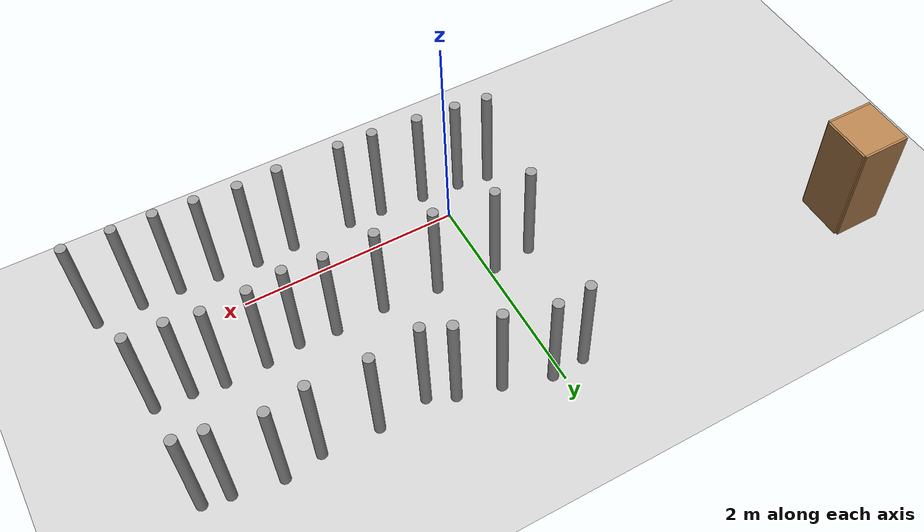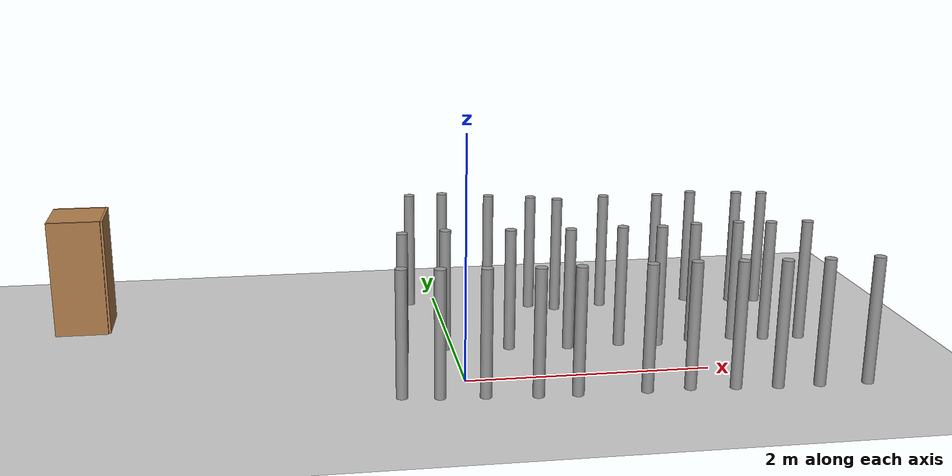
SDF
<sdf version="1.7">
 <world name="default">
  <light name="sun" type="directional">
   <pose>0 0 10 0 -0 0</pose>
   <diffuse>0.8 0.8 0.8 1</diffuse>
   <specular>0.2 0.2 0.2 1</specular>
   <attenuation>
    <range>1000</range>
    <constant>0.9</constant>
    <linear>0.01</linear>
    <quadratic>0.001</quadratic>
   </attenuation>
   <direction>-0.5 0.1 -0.9</direction>
   <spot><inner_angle>0</inner_angle><outer_angle>0</outer_angle><falloff>0</falloff></spot>
  </light>
  <model name="ground_plane">
   <static>1</static>
   <link name="link">
    <collision name="collision">
     <geometry><plane><normal>0 0 1</normal><size>100 100</size></plane></geometry>
     <surface><friction><ode><mu>100</mu><mu2>50</mu2></ode></friction></surface>
    </collision>
    <visual name="visual">
     <cast_shadows>0</cast_shadows>
     <geometry><plane><normal>0 0 1</normal><size>100 100</size></plane></geometry>
     <material>
      <script><uri>file://media/materials/scripts/gazebo.material</uri><name>Gazebo/Grey</name></script>
     </material>
    </visual>
   </link>
  </model>
  <gravity>0 0 -9.8</gravity>
  <magnetic_field>6e-06 2.3e-05 -4.2e-05</magnetic_field>
  <atmosphere type="adiabatic"/>
  <physics type="ode">
   <max_step_size>0.001</max_step_size>
   <real_time_factor>1</real_time_factor>
   <real_time_update_rate>1000</real_time_update_rate>
  </physics>
  <scene><ambient>0.4 0.4 0.4 1</ambient><background>0.7 0.7 0.7 1</background><shadows>1</shadows></scene>
  <spherical_coordinates>
   <surface_model>EARTH_WGS84</surface_model>
   <latitude_deg>0</latitude_deg>
   <longitude_deg>0</longitude_deg>
   <elevation>0</elevation>
   <heading_deg>0</heading_deg>
  </spherical_coordinates>
  <model name="cabinet">
   <static>1</static>
   <link name="cabinet_bottom_plate">
    <inertial>
     <pose>0 0 -1 0 -0 0</pose>
     <inertia><ixx>2.05</ixx><ixy>0</ixy><ixz>0</ixz><iyy>2.05</iyy><iyz>0</iyz><izz>2.05</izz></inertia>
     <mass>25</mass>
    </inertial>
    <collision name="cabinet_bottom_plate_geom">
     <pose>0 0 0.01 0 -0 0</pose>
     <geometry><box><size>0.45 0.45 0.02</size></box></geometry>
    </collision>
    <visual name="cabinet_bottom_plate_geom_visual">
     <pose>0 0 0.01 0 -0 0</pose>
     <geometry><box><size>0.45 0.45 0.02</size></box></geometry>
     <material>
      <script><uri>file://media/materials/scripts/gazebo.material</uri><name>Gazebo/Wood</name></script>
     </material>
    </visual>
    <collision name="cabinet_bottom_plate_geom_cabinet_back_plate">
     <pose>0.235 0 0.51 0 -0 0</pose>
     <geometry><box><size>0.02 0.45 1.02</size></box></geometry>
    </collision>
    <visual name="cabinet_bottom_plate_geom_cabinet_back_plate_visual">
     <pose>0.235 0 0.51 0 -0 0</pose>
     <geometry><box><size>0.02 0.45 1.02</size></box></geometry>
     <material>
      <script><uri>file://media/materials/scripts/gazebo.material</uri><name>Gazebo/Wood</name></script>
     </material>
    </visual>
    <collision name="cabinet_bottom_plate_geom_cabinet_left_plate">
     <pose>0 0.235 0.51 0 -0 0</pose>
     <geometry><box><size>0.45 0.02 1.02</size></box></geometry>
    </collision>
    <visual name="cabinet_bottom_plate_geom_cabinet_left_plate_visual">
     <pose>0 0.235 0.51 0 -0 0</pose>
     <geometry><box><size>0.45 0.02 1.02</size></box></geometry>
     <material>
      <script><uri>file://media/materials/scripts/gazebo.material</uri><name>Gazebo/Wood</name></script>
     </material>
    </visual>
    <collision name="cabinet_bottom_plate_geom_cabinet_middle_plate">
     <pose>0 0 0.51 0 -0 0</pose>
     <geometry><box><size>0.45 0.45 0.02</size></box></geometry>
    </collision>
    <visual name="cabinet_bottom_plate_geom_cabinet_middle_plate_visual">
     <pose>0 0 0.51 0 -0 0</pose>
     <geometry><box><size>0.45 0.45 0.02</size></box></geometry>
     <material>
      <script><uri>file://media/materials/scripts/gazebo.material</uri><name>Gazebo/Wood</name></script>
     </material>
    </visual>
    <collision name="cabinet_bottom_plate_geom_cabinet_right_plate">
     <pose>0 -0.235 0.51 0 -0 0</pose>
     <geometry><box><size>0.45 0.02 1.02</size></box></geometry>
    </collision>
    <visual name="cabinet_bottom_plate_geom_cabinet_right_plate_visual">
     <pose>0 -0.235 0.51 0 -0 0</pose>
     <geometry><box><size>0.45 0.02 1.02</size></box></geometry>
     <material>
      <script><uri>file://media/materials/scripts/gazebo.material</uri><name>Gazebo/Wood</name></script>
     </material>
    </visual>
    <collision name="cabinet_bottom_plate_geom_cabinet_top_plate">
     <pose>0 0 1.01 0 -0 0</pose>
     <geometry><box><size>0.45 0.45 0.02</size></box></geometry>
    </collision>
    <visual name="cabinet_bottom_plate_geom_cabinet_top_plate_visual">
     <pose>0 0 1.01 0 -0 0</pose>
     <geometry><box><size>0.45 0.45 0.02</size></box></geometry>
     <material>
      <script><uri>file://media/materials/scripts/gazebo.material</uri><name>Gazebo/Wood</name></script>
     </material>
    </visual>
   </link>
   <pose>-3.15295 1.69225 0 0 -0 0</pose>
  </model>
  <model name="bar">
   <link name="link_0">
    <inertial>
     <mass>0.00953712</mass>
     <inertia>
      <ixx>0.000924862</ixx>
      <ixy>0</ixy>
      <ixz>0</ixz>
      <iyy>0.000924862</iyy>
      <iyz>0</iyz>
      <izz>1.05584e-05</izz>
     </inertia>
    </inertial>
    <visual name="visual">
     <geometry><cylinder><radius>0.0470549</radius><length>1.07567</length></cylinder></geometry>
     <material>
      <lighting>1</lighting>
      <script><uri>file://media/materials/scripts/gazebo.material</uri><name>Gazebo/Grey</name></script>
      <shader type="pixel"><normal_map>__default__</normal_map></shader>
     </material>
    </visual>
    <collision name="collision">
     <geometry><cylinder><radius>0.047055</radius><length>1.07567</length></cylinder></geometry>
     <surface>
      <friction>
       <ode><mu>1</mu><mu2>1</mu2><fdir1>0 0 0</fdir1><slip1>0</slip1><slip2>0</slip2></ode>
       <torsional>
        <coefficient>1</coefficient>
        <patch_radius>0</patch_radius>
        <surface_radius>0</surface_radius>
        <use_patch_radius>1</use_patch_radius>
        <ode><slip>0</slip></ode>
       </torsional>
      </friction>
      <bounce><restitution_coefficient>0</restitution_coefficient><threshold>1e+06</threshold></bounce>
      <contact>
       <collide_without_contact>0</collide_without_contact>
       <collide_without_contact_bitmask>1</collide_without_contact_bitmask>
       <collide_bitmask>1</collide_bitmask>
       <ode>
        <soft_cfm>0</soft_cfm>
        <soft_erp>0.2</soft_erp>
        <kp>1e+13</kp>
        <kd>1</kd>
        <max_vel>0.01</max_vel>
        <min_depth>0</min_depth>
       </ode>
       <bullet>
        <split_impulse>1</split_impulse>
        <split_impulse_penetration_threshold>-0.01</split_impulse_penetration_threshold>
        <soft_cfm>0</soft_cfm>
        <soft_erp>0.2</soft_erp>
        <kp>1e+13</kp>
        <kd>1</kd>
       </bullet>
      </contact>
     </surface>
    </collision>
   </link>
   <static>0</static>
   <pose>-0.534568 -0.241231 0.5 0 -0 0</pose>
  </model>
  <model name="bar_clone">
   <link name="link_0">
    <inertial>
     <mass>0.00953712</mass>
     <inertia>
      <ixx>0.000924862</ixx>
      <ixy>0</ixy>
      <ixz>0</ixz>
      <iyy>0.000924862</iyy>
      <iyz>0</iyz>
      <izz>1.05584e-05</izz>
     </inertia>
    </inertial>
    <visual name="visual">
     <geometry><cylinder><radius>0.0470549</radius><length>1.07567</length></cylinder></geometry>
     <material>
      <lighting>1</lighting>
      <script><uri>file://media/materials/scripts/gazebo.material</uri><name>Gazebo/Grey</name></script>
      <shader type="pixel"><normal_map>__default__</normal_map></shader>
     </material>
    </visual>
    <collision name="collision">
     <geometry><cylinder><radius>0.047055</radius><length>1.07567</length></cylinder></geometry>
     <surface>
      <friction>
       <ode><mu>1</mu><mu2>1</mu2><fdir1>0 0 0</fdir1><slip1>0</slip1><slip2>0</slip2></ode>
       <torsional>
        <coefficient>1</coefficient>
        <patch_radius>0</patch_radius>
        <surface_radius>0</surface_radius>
        <use_patch_radius>1</use_patch_radius>
        <ode><slip>0</slip></ode>
       </torsional>
      </friction>
      <bounce><restitution_coefficient>0</restitution_coefficient><threshold>1e+06</threshold></bounce>
      <contact>
       <collide_without_contact>0</collide_without_contact>
       <collide_without_contact_bitmask>1</collide_without_contact_bitmask>
       <collide_bitmask>1</collide_bitmask>
       <ode>
        <soft_cfm>0</soft_cfm>
        <soft_erp>0.2</soft_erp>
        <kp>1e+13</kp>
        <kd>1</kd>
        <max_vel>0.01</max_vel>
        <min_depth>0</min_depth>
       </ode>
       <bullet>
        <split_impulse>1</split_impulse>
        <split_impulse_penetration_threshold>-0.01</split_impulse_penetration_threshold>
        <soft_cfm>0</soft_cfm>
        <soft_erp>0.2</soft_erp>
        <kp>1e+13</kp>
        <kd>1</kd>
       </bullet>
      </contact>
     </surface>
    </collision>
   </link>
   <static>0</static>
   <pose>-0.243707 -0.28566 0.5 0 -0 0</pose>
  </model>
  <model name="bar_clone_0">
   <link name="link_0">
    <inertial>
     <mass>0.00953712</mass>
     <inertia>
      <ixx>0.000924862</ixx>
      <ixy>0</ixy>
      <ixz>0</ixz>
      <iyy>0.000924862</iyy>
      <iyz>0</iyz>
      <izz>1.05584e-05</izz>
     </inertia>
    </inertial>
    <visual name="visual">
     <geometry><cylinder><radius>0.0470549</radius><length>1.07567</length></cylinder></geometry>
     <material>
      <lighting>1</lighting>
      <script><uri>file://media/materials/scripts/gazebo.material</uri><name>Gazebo/Grey</name></script>
      <shader type="pixel"><normal_map>__default__</normal_map></shader>
     </material>
    </visual>
    <collision name="collision">
     <geometry><cylinder><radius>0.047055</radius><length>1.07567</length></cylinder></geometry>
     <surface>
      <friction>
       <ode><mu>1</mu><mu2>1</mu2><fdir1>0 0 0</fdir1><slip1>0</slip1><slip2>0</slip2></ode>
       <torsional>
        <coefficient>1</coefficient>
        <patch_radius>0</patch_radius>
        <surface_radius>0</surface_radius>
        <use_patch_radius>1</use_patch_radius>
        <ode><slip>0</slip></ode>
       </torsional>
      </friction>
      <bounce><restitution_coefficient>0</restitution_coefficient><threshold>1e+06</threshold></bounce>
      <contact>
       <collide_without_contact>0</collide_without_contact>
       <collide_without_contact_bitmask>1</collide_without_contact_bitmask>
       <collide_bitmask>1</collide_bitmask>
       <ode>
        <soft_cfm>0</soft_cfm>
        <soft_erp>0.2</soft_erp>
        <kp>1e+13</kp>
        <kd>1</kd>
        <max_vel>0.01</max_vel>
        <min_depth>0</min_depth>
       </ode>
       <bullet>
        <split_impulse>1</split_impulse>
        <split_impulse_penetration_threshold>-0.01</split_impulse_penetration_threshold>
        <soft_cfm>0</soft_cfm>
        <soft_erp>0.2</soft_erp>
        <kp>1e+13</kp>
        <kd>1</kd>
       </bullet>
      </contact>
     </surface>
    </collision>
   </link>
   <static>0</static>
   <pose>0.109107 -0.316325 0.5 0 -0 0</pose>
  </model>
  <model name="bar_clone_1">
   <link name="link_0">
    <inertial>
     <mass>0.00953712</mass>
     <inertia>
      <ixx>0.000924862</ixx>
      <ixy>0</ixy>
      <ixz>0</ixz>
      <iyy>0.000924862</iyy>
      <iyz>0</iyz>
      <izz>1.05584e-05</izz>
     </inertia>
    </inertial>
    <visual name="visual">
     <geometry><cylinder><radius>0.0470549</radius><length>1.07567</length></cylinder></geometry>
     <material>
      <lighting>1</lighting>
      <script><uri>file://media/materials/scripts/gazebo.material</uri><name>Gazebo/Grey</name></script>
      <shader type="pixel"><normal_map>__default__</normal_map></shader>
     </material>
    </visual>
    <collision name="collision">
     <geometry><cylinder><radius>0.047055</radius><length>1.07567</length></cylinder></geometry>
     <surface>
      <friction>
       <ode><mu>1</mu><mu2>1</mu2><fdir1>0 0 0</fdir1><slip1>0</slip1><slip2>0</slip2></ode>
       <torsional>
        <coefficient>1</coefficient>
        <patch_radius>0</patch_radius>
        <surface_radius>0</surface_radius>
        <use_patch_radius>1</use_patch_radius>
        <ode><slip>0</slip></ode>
       </torsional>
      </friction>
      <bounce><restitution_coefficient>0</restitution_coefficient><threshold>1e+06</threshold></bounce>
      <contact>
       <collide_without_contact>0</collide_without_contact>
       <collide_without_contact_bitmask>1</collide_without_contact_bitmask>
       <collide_bitmask>1</collide_bitmask>
       <ode>
        <soft_cfm>0</soft_cfm>
        <soft_erp>0.2</soft_erp>
        <kp>1e+13</kp>
        <kd>1</kd>
        <max_vel>0.01</max_vel>
        <min_depth>0</min_depth>
       </ode>
       <bullet>
        <split_impulse>1</split_impulse>
        <split_impulse_penetration_threshold>-0.01</split_impulse_penetration_threshold>
        <soft_cfm>0</soft_cfm>
        <soft_erp>0.2</soft_erp>
        <kp>1e+13</kp>
        <kd>1</kd>
       </bullet>
      </contact>
     </surface>
    </collision>
   </link>
   <static>0</static>
   <pose>0.513716 -0.357578 0.5 0 -0 0</pose>
  </model>
  <model name="bar_clone_2">
   <link name="link_0">
    <inertial>
     <mass>0.00953712</mass>
     <inertia>
      <ixx>0.000924862</ixx>
      <ixy>0</ixy>
      <ixz>0</ixz>
      <iyy>0.000924862</iyy>
      <iyz>0</iyz>
      <izz>1.05584e-05</izz>
     </inertia>
    </inertial>
    <visual name="visual">
     <geometry><cylinder><radius>0.0470549</radius><length>1.07567</length></cylinder></geometry>
     <material>
      <lighting>1</lighting>
      <script><uri>file://media/materials/scripts/gazebo.material</uri><name>Gazebo/Grey</name></script>
      <shader type="pixel"><normal_map>__default__</normal_map></shader>
     </material>
    </visual>
    <collision name="collision">
     <geometry><cylinder><radius>0.047055</radius><length>1.07567</length></cylinder></geometry>
     <surface>
      <friction>
       <ode><mu>1</mu><mu2>1</mu2><fdir1>0 0 0</fdir1><slip1>0</slip1><slip2>0</slip2></ode>
       <torsional>
        <coefficient>1</coefficient>
        <patch_radius>0</patch_radius>
        <surface_radius>0</surface_radius>
        <use_patch_radius>1</use_patch_radius>
        <ode><slip>0</slip></ode>
       </torsional>
      </friction>
      <bounce><restitution_coefficient>0</restitution_coefficient><threshold>1e+06</threshold></bounce>
      <contact>
       <collide_without_contact>0</collide_without_contact>
       <collide_without_contact_bitmask>1</collide_without_contact_bitmask>
       <collide_bitmask>1</collide_bitmask>
       <ode>
        <soft_cfm>0</soft_cfm>
        <soft_erp>0.2</soft_erp>
        <kp>1e+13</kp>
        <kd>1</kd>
        <max_vel>0.01</max_vel>
        <min_depth>0</min_depth>
       </ode>
       <bullet>
        <split_impulse>1</split_impulse>
        <split_impulse_penetration_threshold>-0.01</split_impulse_penetration_threshold>
        <soft_cfm>0</soft_cfm>
        <soft_erp>0.2</soft_erp>
        <kp>1e+13</kp>
        <kd>1</kd>
       </bullet>
      </contact>
     </surface>
    </collision>
   </link>
   <static>0</static>
   <pose>0.824267 -0.369103 0.5 0 -0 0</pose>
  </model>
  <model name="bar_clone_3">
   <link name="link_0">
    <inertial>
     <mass>0.00953712</mass>
     <inertia>
      <ixx>0.000924862</ixx>
      <ixy>0</ixy>
      <ixz>0</ixz>
      <iyy>0.000924862</iyy>
      <iyz>0</iyz>
      <izz>1.05584e-05</izz>
     </inertia>
    </inertial>
    <visual name="visual">
     <geometry><cylinder><radius>0.0470549</radius><length>1.07567</length></cylinder></geometry>
     <material>
      <lighting>1</lighting>
      <script><uri>file://media/materials/scripts/gazebo.material</uri><name>Gazebo/Grey</name></script>
      <shader type="pixel"><normal_map>__default__</normal_map></shader>
     </material>
    </visual>
    <collision name="collision">
     <geometry><cylinder><radius>0.047055</radius><length>1.07567</length></cylinder></geometry>
     <surface>
      <friction>
       <ode><mu>1</mu><mu2>1</mu2><fdir1>0 0 0</fdir1><slip1>0</slip1><slip2>0</slip2></ode>
       <torsional>
        <coefficient>1</coefficient>
        <patch_radius>0</patch_radius>
        <surface_radius>0</surface_radius>
        <use_patch_radius>1</use_patch_radius>
        <ode><slip>0</slip></ode>
       </torsional>
      </friction>
      <bounce><restitution_coefficient>0</restitution_coefficient><threshold>1e+06</threshold></bounce>
      <contact>
       <collide_without_contact>0</collide_without_contact>
       <collide_without_contact_bitmask>1</collide_without_contact_bitmask>
       <collide_bitmask>1</collide_bitmask>
       <ode>
        <soft_cfm>0</soft_cfm>
        <soft_erp>0.2</soft_erp>
        <kp>1e+13</kp>
        <kd>1</kd>
        <max_vel>0.01</max_vel>
        <min_depth>0</min_depth>
       </ode>
       <bullet>
        <split_impulse>1</split_impulse>
        <split_impulse_penetration_threshold>-0.01</split_impulse_penetration_threshold>
        <soft_cfm>0</soft_cfm>
        <soft_erp>0.2</soft_erp>
        <kp>1e+13</kp>
        <kd>1</kd>
       </bullet>
      </contact>
     </surface>
    </collision>
   </link>
   <static>0</static>
   <pose>1.37451 -0.379347 0.5 0 -0 0</pose>
  </model>
  <model name="bar_clone_4">
   <link name="link_0">
    <inertial>
     <mass>0.00953712</mass>
     <inertia>
      <ixx>0.000924862</ixx>
      <ixy>0</ixy>
      <ixz>0</ixz>
      <iyy>0.000924862</iyy>
      <iyz>0</iyz>
      <izz>1.05584e-05</izz>
     </inertia>
    </inertial>
    <visual name="visual">
     <geometry><cylinder><radius>0.0470549</radius><length>1.07567</length></cylinder></geometry>
     <material>
      <lighting>1</lighting>
      <script><uri>file://media/materials/scripts/gazebo.material</uri><name>Gazebo/Grey</name></script>
      <shader type="pixel"><normal_map>__default__</normal_map></shader>
     </material>
    </visual>
    <collision name="collision">
     <geometry><cylinder><radius>0.047055</radius><length>1.07567</length></cylinder></geometry>
     <surface>
      <friction>
       <ode><mu>1</mu><mu2>1</mu2><fdir1>0 0 0</fdir1><slip1>0</slip1><slip2>0</slip2></ode>
       <torsional>
        <coefficient>1</coefficient>
        <patch_radius>0</patch_radius>
        <surface_radius>0</surface_radius>
        <use_patch_radius>1</use_patch_radius>
        <ode><slip>0</slip></ode>
       </torsional>
      </friction>
      <bounce><restitution_coefficient>0</restitution_coefficient><threshold>1e+06</threshold></bounce>
      <contact>
       <collide_without_contact>0</collide_without_contact>
       <collide_without_contact_bitmask>1</collide_without_contact_bitmask>
       <collide_bitmask>1</collide_bitmask>
       <ode>
        <soft_cfm>0</soft_cfm>
        <soft_erp>0.2</soft_erp>
        <kp>1e+13</kp>
        <kd>1</kd>
        <max_vel>0.01</max_vel>
        <min_depth>0</min_depth>
       </ode>
       <bullet>
        <split_impulse>1</split_impulse>
        <split_impulse_penetration_threshold>-0.01</split_impulse_penetration_threshold>
        <soft_cfm>0</soft_cfm>
        <soft_erp>0.2</soft_erp>
        <kp>1e+13</kp>
        <kd>1</kd>
       </bullet>
      </contact>
     </surface>
    </collision>
   </link>
   <static>0</static>
   <pose>1.72439 -0.372293 0.5 0 -0 0</pose>
  </model>
  <model name="bar_clone_5">
   <link name="link_0">
    <inertial>
     <mass>0.00953712</mass>
     <inertia>
      <ixx>0.000924862</ixx>
      <ixy>0</ixy>
      <ixz>0</ixz>
      <iyy>0.000924862</iyy>
      <iyz>0</iyz>
      <izz>1.05584e-05</izz>
     </inertia>
    </inertial>
    <visual name="visual">
     <geometry><cylinder><radius>0.0470549</radius><length>1.07567</length></cylinder></geometry>
     <material>
      <lighting>1</lighting>
      <script><uri>file://media/materials/scripts/gazebo.material</uri><name>Gazebo/Grey</name></script>
      <shader type="pixel"><normal_map>__default__</normal_map></shader>
     </material>
    </visual>
    <collision name="collision">
     <geometry><cylinder><radius>0.047055</radius><length>1.07567</length></cylinder></geometry>
     <surface>
      <friction>
       <ode><mu>1</mu><mu2>1</mu2><fdir1>0 0 0</fdir1><slip1>0</slip1><slip2>0</slip2></ode>
       <torsional>
        <coefficient>1</coefficient>
        <patch_radius>0</patch_radius>
        <surface_radius>0</surface_radius>
        <use_patch_radius>1</use_patch_radius>
        <ode><slip>0</slip></ode>
       </torsional>
      </friction>
      <bounce><restitution_coefficient>0</restitution_coefficient><threshold>1e+06</threshold></bounce>
      <contact>
       <collide_without_contact>0</collide_without_contact>
       <collide_without_contact_bitmask>1</collide_without_contact_bitmask>
       <collide_bitmask>1</collide_bitmask>
       <ode>
        <soft_cfm>0</soft_cfm>
        <soft_erp>0.2</soft_erp>
        <kp>1e+13</kp>
        <kd>1</kd>
        <max_vel>0.01</max_vel>
        <min_depth>0</min_depth>
       </ode>
       <bullet>
        <split_impulse>1</split_impulse>
        <split_impulse_penetration_threshold>-0.01</split_impulse_penetration_threshold>
        <soft_cfm>0</soft_cfm>
        <soft_erp>0.2</soft_erp>
        <kp>1e+13</kp>
        <kd>1</kd>
       </bullet>
      </contact>
     </surface>
    </collision>
   </link>
   <static>0</static>
   <pose>2.08498 -0.403404 0.5 0 -0 0</pose>
  </model>
  <model name="bar_clone_6">
   <link name="link_0">
    <inertial>
     <mass>0.00953712</mass>
     <inertia>
      <ixx>0.000924862</ixx>
      <ixy>0</ixy>
      <ixz>0</ixz>
      <iyy>0.000924862</iyy>
      <iyz>0</iyz>
      <izz>1.05584e-05</izz>
     </inertia>
    </inertial>
    <visual name="visual">
     <geometry><cylinder><radius>0.0470549</radius><length>1.07567</length></cylinder></geometry>
     <material>
      <lighting>1</lighting>
      <script><uri>file://media/materials/scripts/gazebo.material</uri><name>Gazebo/Grey</name></script>
      <shader type="pixel"><normal_map>__default__</normal_map></shader>
     </material>
    </visual>
    <collision name="collision">
     <geometry><cylinder><radius>0.047055</radius><length>1.07567</length></cylinder></geometry>
     <surface>
      <friction>
       <ode><mu>1</mu><mu2>1</mu2><fdir1>0 0 0</fdir1><slip1>0</slip1><slip2>0</slip2></ode>
       <torsional>
        <coefficient>1</coefficient>
        <patch_radius>0</patch_radius>
        <surface_radius>0</surface_radius>
        <use_patch_radius>1</use_patch_radius>
        <ode><slip>0</slip></ode>
       </torsional>
      </friction>
      <bounce><restitution_coefficient>0</restitution_coefficient><threshold>1e+06</threshold></bounce>
      <contact>
       <collide_without_contact>0</collide_without_contact>
       <collide_without_contact_bitmask>1</collide_without_contact_bitmask>
       <collide_bitmask>1</collide_bitmask>
       <ode>
        <soft_cfm>0</soft_cfm>
        <soft_erp>0.2</soft_erp>
        <kp>1e+13</kp>
        <kd>1</kd>
        <max_vel>0.01</max_vel>
        <min_depth>0</min_depth>
       </ode>
       <bullet>
        <split_impulse>1</split_impulse>
        <split_impulse_penetration_threshold>-0.01</split_impulse_penetration_threshold>
        <soft_cfm>0</soft_cfm>
        <soft_erp>0.2</soft_erp>
        <kp>1e+13</kp>
        <kd>1</kd>
       </bullet>
      </contact>
     </surface>
    </collision>
   </link>
   <static>0</static>
   <pose>2.4203 -0.432616 0.5 0 -0 0</pose>
  </model>
  <model name="bar_clone_7">
   <link name="link_0">
    <inertial>
     <mass>0.00953712</mass>
     <inertia>
      <ixx>0.000924862</ixx>
      <ixy>0</ixy>
      <ixz>0</ixz>
      <iyy>0.000924862</iyy>
      <iyz>0</iyz>
      <izz>1.05584e-05</izz>
     </inertia>
    </inertial>
    <visual name="visual">
     <geometry><cylinder><radius>0.0470549</radius><length>1.07567</length></cylinder></geometry>
     <material>
      <lighting>1</lighting>
      <script><uri>file://media/materials/scripts/gazebo.material</uri><name>Gazebo/Grey</name></script>
      <shader type="pixel"><normal_map>__default__</normal_map></shader>
     </material>
    </visual>
    <collision name="collision">
     <geometry><cylinder><radius>0.047055</radius><length>1.07567</length></cylinder></geometry>
     <surface>
      <friction>
       <ode><mu>1</mu><mu2>1</mu2><fdir1>0 0 0</fdir1><slip1>0</slip1><slip2>0</slip2></ode>
       <torsional>
        <coefficient>1</coefficient>
        <patch_radius>0</patch_radius>
        <surface_radius>0</surface_radius>
        <use_patch_radius>1</use_patch_radius>
        <ode><slip>0</slip></ode>
       </torsional>
      </friction>
      <bounce><restitution_coefficient>0</restitution_coefficient><threshold>1e+06</threshold></bounce>
      <contact>
       <collide_without_contact>0</collide_without_contact>
       <collide_without_contact_bitmask>1</collide_without_contact_bitmask>
       <collide_bitmask>1</collide_bitmask>
       <ode>
        <soft_cfm>0</soft_cfm>
        <soft_erp>0.2</soft_erp>
        <kp>1e+13</kp>
        <kd>1</kd>
        <max_vel>0.01</max_vel>
        <min_depth>0</min_depth>
       </ode>
       <bullet>
        <split_impulse>1</split_impulse>
        <split_impulse_penetration_threshold>-0.01</split_impulse_penetration_threshold>
        <soft_cfm>0</soft_cfm>
        <soft_erp>0.2</soft_erp>
        <kp>1e+13</kp>
        <kd>1</kd>
       </bullet>
      </contact>
     </surface>
    </collision>
   </link>
   <static>0</static>
   <pose>2.76123 -0.439279 0.5 0 -0 0</pose>
  </model>
  <model name="bar_clone_8">
   <link name="link_0">
    <inertial>
     <mass>0.00953712</mass>
     <inertia>
      <ixx>0.000924862</ixx>
      <ixy>0</ixy>
      <ixz>0</ixz>
      <iyy>0.000924862</iyy>
      <iyz>0</iyz>
      <izz>1.05584e-05</izz>
     </inertia>
    </inertial>
    <visual name="visual">
     <geometry><cylinder><radius>0.0470549</radius><length>1.07567</length></cylinder></geometry>
     <material>
      <lighting>1</lighting>
      <script><uri>file://media/materials/scripts/gazebo.material</uri><name>Gazebo/Grey</name></script>
      <shader type="pixel"><normal_map>__default__</normal_map></shader>
     </material>
    </visual>
    <collision name="collision">
     <geometry><cylinder><radius>0.047055</radius><length>1.07567</length></cylinder></geometry>
     <surface>
      <friction>
       <ode><mu>1</mu><mu2>1</mu2><fdir1>0 0 0</fdir1><slip1>0</slip1><slip2>0</slip2></ode>
       <torsional>
        <coefficient>1</coefficient>
        <patch_radius>0</patch_radius>
        <surface_radius>0</surface_radius>
        <use_patch_radius>1</use_patch_radius>
        <ode><slip>0</slip></ode>
       </torsional>
      </friction>
      <bounce><restitution_coefficient>0</restitution_coefficient><threshold>1e+06</threshold></bounce>
      <contact>
       <collide_without_contact>0</collide_without_contact>
       <collide_without_contact_bitmask>1</collide_without_contact_bitmask>
       <collide_bitmask>1</collide_bitmask>
       <ode>
        <soft_cfm>0</soft_cfm>
        <soft_erp>0.2</soft_erp>
        <kp>1e+13</kp>
        <kd>1</kd>
        <max_vel>0.01</max_vel>
        <min_depth>0</min_depth>
       </ode>
       <bullet>
        <split_impulse>1</split_impulse>
        <split_impulse_penetration_threshold>-0.01</split_impulse_penetration_threshold>
        <soft_cfm>0</soft_cfm>
        <soft_erp>0.2</soft_erp>
        <kp>1e+13</kp>
        <kd>1</kd>
       </bullet>
      </contact>
     </surface>
    </collision>
   </link>
   <static>0</static>
   <pose>3.15901 -0.447083 0.5 0 -0 0</pose>
  </model>
  <model name="bar_clone_9">
   <link name="link_0">
    <inertial>
     <mass>0.00953712</mass>
     <inertia>
      <ixx>0.000924862</ixx>
      <ixy>0</ixy>
      <ixz>0</ixz>
      <iyy>0.000924862</iyy>
      <iyz>0</iyz>
      <izz>1.05584e-05</izz>
     </inertia>
    </inertial>
    <visual name="visual">
     <geometry><cylinder><radius>0.0470549</radius><length>1.07567</length></cylinder></geometry>
     <material>
      <lighting>1</lighting>
      <script><uri>file://media/materials/scripts/gazebo.material</uri><name>Gazebo/Grey</name></script>
      <shader type="pixel"><normal_map>__default__</normal_map></shader>
     </material>
    </visual>
    <collision name="collision">
     <geometry><cylinder><radius>0.047055</radius><length>1.07567</length></cylinder></geometry>
     <surface>
      <friction>
       <ode><mu>1</mu><mu2>1</mu2><fdir1>0 0 0</fdir1><slip1>0</slip1><slip2>0</slip2></ode>
       <torsional>
        <coefficient>1</coefficient>
        <patch_radius>0</patch_radius>
        <surface_radius>0</surface_radius>
        <use_patch_radius>1</use_patch_radius>
        <ode><slip>0</slip></ode>
       </torsional>
      </friction>
      <bounce><restitution_coefficient>0</restitution_coefficient><threshold>1e+06</threshold></bounce>
      <contact>
       <collide_without_contact>0</collide_without_contact>
       <collide_without_contact_bitmask>1</collide_without_contact_bitmask>
       <collide_bitmask>1</collide_bitmask>
       <ode>
        <soft_cfm>0</soft_cfm>
        <soft_erp>0.2</soft_erp>
        <kp>1e+13</kp>
        <kd>1</kd>
        <max_vel>0.01</max_vel>
        <min_depth>0</min_depth>
       </ode>
       <bullet>
        <split_impulse>1</split_impulse>
        <split_impulse_penetration_threshold>-0.01</split_impulse_penetration_threshold>
        <soft_cfm>0</soft_cfm>
        <soft_erp>0.2</soft_erp>
        <kp>1e+13</kp>
        <kd>1</kd>
       </bullet>
      </contact>
     </surface>
    </collision>
   </link>
   <static>0</static>
   <pose>-0.426532 0.68948 0.5 0 -0 0</pose>
  </model>
  <model name="bar_clone_10">
   <link name="link_0">
    <inertial>
     <mass>0.00953712</mass>
     <inertia>
      <ixx>0.000924862</ixx>
      <ixy>0</ixy>
      <ixz>0</ixz>
      <iyy>0.000924862</iyy>
      <iyz>0</iyz>
      <izz>1.05584e-05</izz>
     </inertia>
    </inertial>
    <visual name="visual">
     <geometry><cylinder><radius>0.0470549</radius><length>1.07567</length></cylinder></geometry>
     <material>
      <lighting>1</lighting>
      <script><uri>file://media/materials/scripts/gazebo.material</uri><name>Gazebo/Grey</name></script>
      <shader type="pixel"><normal_map>__default__</normal_map></shader>
     </material>
    </visual>
    <collision name="collision">
     <geometry><cylinder><radius>0.047055</radius><length>1.07567</length></cylinder></geometry>
     <surface>
      <friction>
       <ode><mu>1</mu><mu2>1</mu2><fdir1>0 0 0</fdir1><slip1>0</slip1><slip2>0</slip2></ode>
       <torsional>
        <coefficient>1</coefficient>
        <patch_radius>0</patch_radius>
        <surface_radius>0</surface_radius>
        <use_patch_radius>1</use_patch_radius>
        <ode><slip>0</slip></ode>
       </torsional>
      </friction>
      <bounce><restitution_coefficient>0</restitution_coefficient><threshold>1e+06</threshold></bounce>
      <contact>
       <collide_without_contact>0</collide_without_contact>
       <collide_without_contact_bitmask>1</collide_without_contact_bitmask>
       <collide_bitmask>1</collide_bitmask>
       <ode>
        <soft_cfm>0</soft_cfm>
        <soft_erp>0.2</soft_erp>
        <kp>1e+13</kp>
        <kd>1</kd>
        <max_vel>0.01</max_vel>
        <min_depth>0</min_depth>
       </ode>
       <bullet>
        <split_impulse>1</split_impulse>
        <split_impulse_penetration_threshold>-0.01</split_impulse_penetration_threshold>
        <soft_cfm>0</soft_cfm>
        <soft_erp>0.2</soft_erp>
        <kp>1e+13</kp>
        <kd>1</kd>
       </bullet>
      </contact>
     </surface>
    </collision>
   </link>
   <static>0</static>
   <pose>-0.062084 0.72884 0.5 0 -0 0</pose>
  </model>
  <model name="bar_clone_11">
   <link name="link_0">
    <inertial>
     <mass>0.00953712</mass>
     <inertia>
      <ixx>0.000924862</ixx>
      <ixy>0</ixy>
      <ixz>0</ixz>
      <iyy>0.000924862</iyy>
      <iyz>0</iyz>
      <izz>1.05584e-05</izz>
     </inertia>
    </inertial>
    <visual name="visual">
     <geometry><cylinder><radius>0.0470549</radius><length>1.07567</length></cylinder></geometry>
     <material>
      <lighting>1</lighting>
      <script><uri>file://media/materials/scripts/gazebo.material</uri><name>Gazebo/Grey</name></script>
      <shader type="pixel"><normal_map>__default__</normal_map></shader>
     </material>
    </visual>
    <collision name="collision">
     <geometry><cylinder><radius>0.047055</radius><length>1.07567</length></cylinder></geometry>
     <surface>
      <friction>
       <ode><mu>1</mu><mu2>1</mu2><fdir1>0 0 0</fdir1><slip1>0</slip1><slip2>0</slip2></ode>
       <torsional>
        <coefficient>1</coefficient>
        <patch_radius>0</patch_radius>
        <surface_radius>0</surface_radius>
        <use_patch_radius>1</use_patch_radius>
        <ode><slip>0</slip></ode>
       </torsional>
      </friction>
      <bounce><restitution_coefficient>0</restitution_coefficient><threshold>1e+06</threshold></bounce>
      <contact>
       <collide_without_contact>0</collide_without_contact>
       <collide_without_contact_bitmask>1</collide_without_contact_bitmask>
       <collide_bitmask>1</collide_bitmask>
       <ode>
        <soft_cfm>0</soft_cfm>
        <soft_erp>0.2</soft_erp>
        <kp>1e+13</kp>
        <kd>1</kd>
        <max_vel>0.01</max_vel>
        <min_depth>0</min_depth>
       </ode>
       <bullet>
        <split_impulse>1</split_impulse>
        <split_impulse_penetration_threshold>-0.01</split_impulse_penetration_threshold>
        <soft_cfm>0</soft_cfm>
        <soft_erp>0.2</soft_erp>
        <kp>1e+13</kp>
        <kd>1</kd>
       </bullet>
      </contact>
     </surface>
    </collision>
   </link>
   <static>0</static>
   <pose>0.478336 0.672013 0.5 0 -0 0</pose>
  </model>
  <model name="bar_clone_12">
   <link name="link_0">
    <inertial>
     <mass>0.00953712</mass>
     <inertia>
      <ixx>0.000924862</ixx>
      <ixy>0</ixy>
      <ixz>0</ixz>
      <iyy>0.000924862</iyy>
      <iyz>0</iyz>
      <izz>1.05584e-05</izz>
     </inertia>
    </inertial>
    <visual name="visual">
     <geometry><cylinder><radius>0.0470549</radius><length>1.07567</length></cylinder></geometry>
     <material>
      <lighting>1</lighting>
      <script><uri>file://media/materials/scripts/gazebo.material</uri><name>Gazebo/Grey</name></script>
      <shader type="pixel"><normal_map>__default__</normal_map></shader>
     </material>
    </visual>
    <collision name="collision">
     <geometry><cylinder><radius>0.047055</radius><length>1.07567</length></cylinder></geometry>
     <surface>
      <friction>
       <ode><mu>1</mu><mu2>1</mu2><fdir1>0 0 0</fdir1><slip1>0</slip1><slip2>0</slip2></ode>
       <torsional>
        <coefficient>1</coefficient>
        <patch_radius>0</patch_radius>
        <surface_radius>0</surface_radius>
        <use_patch_radius>1</use_patch_radius>
        <ode><slip>0</slip></ode>
       </torsional>
      </friction>
      <bounce><restitution_coefficient>0</restitution_coefficient><threshold>1e+06</threshold></bounce>
      <contact>
       <collide_without_contact>0</collide_without_contact>
       <collide_without_contact_bitmask>1</collide_without_contact_bitmask>
       <collide_bitmask>1</collide_bitmask>
       <ode>
        <soft_cfm>0</soft_cfm>
        <soft_erp>0.2</soft_erp>
        <kp>1e+13</kp>
        <kd>1</kd>
        <max_vel>0.01</max_vel>
        <min_depth>0</min_depth>
       </ode>
       <bullet>
        <split_impulse>1</split_impulse>
        <split_impulse_penetration_threshold>-0.01</split_impulse_penetration_threshold>
        <soft_cfm>0</soft_cfm>
        <soft_erp>0.2</soft_erp>
        <kp>1e+13</kp>
        <kd>1</kd>
       </bullet>
      </contact>
     </surface>
    </collision>
   </link>
   <static>0</static>
   <pose>0.976334 0.622558 0.5 0 -0 0</pose>
  </model>
  <model name="bar_clone_13">
   <link name="link_0">
    <inertial>
     <mass>0.00953712</mass>
     <inertia>
      <ixx>0.000924862</ixx>
      <ixy>0</ixy>
      <ixz>0</ixz>
      <iyy>0.000924862</iyy>
      <iyz>0</iyz>
      <izz>1.05584e-05</izz>
     </inertia>
    </inertial>
    <visual name="visual">
     <geometry><cylinder><radius>0.0470549</radius><length>1.07567</length></cylinder></geometry>
     <material>
      <lighting>1</lighting>
      <script><uri>file://media/materials/scripts/gazebo.material</uri><name>Gazebo/Grey</name></script>
      <shader type="pixel"><normal_map>__default__</normal_map></shader>
     </material>
    </visual>
    <collision name="collision">
     <geometry><cylinder><radius>0.047055</radius><length>1.07567</length></cylinder></geometry>
     <surface>
      <friction>
       <ode><mu>1</mu><mu2>1</mu2><fdir1>0 0 0</fdir1><slip1>0</slip1><slip2>0</slip2></ode>
       <torsional>
        <coefficient>1</coefficient>
        <patch_radius>0</patch_radius>
        <surface_radius>0</surface_radius>
        <use_patch_radius>1</use_patch_radius>
        <ode><slip>0</slip></ode>
       </torsional>
      </friction>
      <bounce><restitution_coefficient>0</restitution_coefficient><threshold>1e+06</threshold></bounce>
      <contact>
       <collide_without_contact>0</collide_without_contact>
       <collide_without_contact_bitmask>1</collide_without_contact_bitmask>
       <collide_bitmask>1</collide_bitmask>
       <ode>
        <soft_cfm>0</soft_cfm>
        <soft_erp>0.2</soft_erp>
        <kp>1e+13</kp>
        <kd>1</kd>
        <max_vel>0.01</max_vel>
        <min_depth>0</min_depth>
       </ode>
       <bullet>
        <split_impulse>1</split_impulse>
        <split_impulse_penetration_threshold>-0.01</split_impulse_penetration_threshold>
        <soft_cfm>0</soft_cfm>
        <soft_erp>0.2</soft_erp>
        <kp>1e+13</kp>
        <kd>1</kd>
       </bullet>
      </contact>
     </surface>
    </collision>
   </link>
   <static>0</static>
   <pose>1.42369 0.635486 0.5 0 -0 0</pose>
  </model>
  <model name="bar_clone_14">
   <link name="link_0">
    <inertial>
     <mass>0.00953712</mass>
     <inertia>
      <ixx>0.000924862</ixx>
      <ixy>0</ixy>
      <ixz>0</ixz>
      <iyy>0.000924862</iyy>
      <iyz>0</iyz>
      <izz>1.05584e-05</izz>
     </inertia>
    </inertial>
    <visual name="visual">
     <geometry><cylinder><radius>0.0470549</radius><length>1.07567</length></cylinder></geometry>
     <material>
      <lighting>1</lighting>
      <script><uri>file://media/materials/scripts/gazebo.material</uri><name>Gazebo/Grey</name></script>
      <shader type="pixel"><normal_map>__default__</normal_map></shader>
     </material>
    </visual>
    <collision name="collision">
     <geometry><cylinder><radius>0.047055</radius><length>1.07567</length></cylinder></geometry>
     <surface>
      <friction>
       <ode><mu>1</mu><mu2>1</mu2><fdir1>0 0 0</fdir1><slip1>0</slip1><slip2>0</slip2></ode>
       <torsional>
        <coefficient>1</coefficient>
        <patch_radius>0</patch_radius>
        <surface_radius>0</surface_radius>
        <use_patch_radius>1</use_patch_radius>
        <ode><slip>0</slip></ode>
       </torsional>
      </friction>
      <bounce><restitution_coefficient>0</restitution_coefficient><threshold>1e+06</threshold></bounce>
      <contact>
       <collide_without_contact>0</collide_without_contact>
       <collide_without_contact_bitmask>1</collide_without_contact_bitmask>
       <collide_bitmask>1</collide_bitmask>
       <ode>
        <soft_cfm>0</soft_cfm>
        <soft_erp>0.2</soft_erp>
        <kp>1e+13</kp>
        <kd>1</kd>
        <max_vel>0.01</max_vel>
        <min_depth>0</min_depth>
       </ode>
       <bullet>
        <split_impulse>1</split_impulse>
        <split_impulse_penetration_threshold>-0.01</split_impulse_penetration_threshold>
        <soft_cfm>0</soft_cfm>
        <soft_erp>0.2</soft_erp>
        <kp>1e+13</kp>
        <kd>1</kd>
       </bullet>
      </contact>
     </surface>
    </collision>
   </link>
   <static>0</static>
   <pose>1.75296 0.598302 0.5 0 -0 0</pose>
  </model>
  <model name="bar_clone_15">
   <link name="link_0">
    <inertial>
     <mass>0.00953712</mass>
     <inertia>
      <ixx>0.000924862</ixx>
      <ixy>0</ixy>
      <ixz>0</ixz>
      <iyy>0.000924862</iyy>
      <iyz>0</iyz>
      <izz>1.05584e-05</izz>
     </inertia>
    </inertial>
    <visual name="visual">
     <geometry><cylinder><radius>0.0470549</radius><length>1.07567</length></cylinder></geometry>
     <material>
      <lighting>1</lighting>
      <script><uri>file://media/materials/scripts/gazebo.material</uri><name>Gazebo/Grey</name></script>
      <shader type="pixel"><normal_map>__default__</normal_map></shader>
     </material>
    </visual>
    <collision name="collision">
     <geometry><cylinder><radius>0.047055</radius><length>1.07567</length></cylinder></geometry>
     <surface>
      <friction>
       <ode><mu>1</mu><mu2>1</mu2><fdir1>0 0 0</fdir1><slip1>0</slip1><slip2>0</slip2></ode>
       <torsional>
        <coefficient>1</coefficient>
        <patch_radius>0</patch_radius>
        <surface_radius>0</surface_radius>
        <use_patch_radius>1</use_patch_radius>
        <ode><slip>0</slip></ode>
       </torsional>
      </friction>
      <bounce><restitution_coefficient>0</restitution_coefficient><threshold>1e+06</threshold></bounce>
      <contact>
       <collide_without_contact>0</collide_without_contact>
       <collide_without_contact_bitmask>1</collide_without_contact_bitmask>
       <collide_bitmask>1</collide_bitmask>
       <ode>
        <soft_cfm>0</soft_cfm>
        <soft_erp>0.2</soft_erp>
        <kp>1e+13</kp>
        <kd>1</kd>
        <max_vel>0.01</max_vel>
        <min_depth>0</min_depth>
       </ode>
       <bullet>
        <split_impulse>1</split_impulse>
        <split_impulse_penetration_threshold>-0.01</split_impulse_penetration_threshold>
        <soft_cfm>0</soft_cfm>
        <soft_erp>0.2</soft_erp>
        <kp>1e+13</kp>
        <kd>1</kd>
       </bullet>
      </contact>
     </surface>
    </collision>
   </link>
   <static>0</static>
   <pose>2.05936 0.640918 0.5 0 -0 0</pose>
  </model>
  <model name="bar_clone_16">
   <link name="link_0">
    <inertial>
     <mass>0.00953712</mass>
     <inertia>
      <ixx>0.000924862</ixx>
      <ixy>0</ixy>
      <ixz>0</ixz>
      <iyy>0.000924862</iyy>
      <iyz>0</iyz>
      <izz>1.05584e-05</izz>
     </inertia>
    </inertial>
    <visual name="visual">
     <geometry><cylinder><radius>0.0470549</radius><length>1.07567</length></cylinder></geometry>
     <material>
      <lighting>1</lighting>
      <script><uri>file://media/materials/scripts/gazebo.material</uri><name>Gazebo/Grey</name></script>
      <shader type="pixel"><normal_map>__default__</normal_map></shader>
     </material>
    </visual>
    <collision name="collision">
     <geometry><cylinder><radius>0.047055</radius><length>1.07567</length></cylinder></geometry>
     <surface>
      <friction>
       <ode><mu>1</mu><mu2>1</mu2><fdir1>0 0 0</fdir1><slip1>0</slip1><slip2>0</slip2></ode>
       <torsional>
        <coefficient>1</coefficient>
        <patch_radius>0</patch_radius>
        <surface_radius>0</surface_radius>
        <use_patch_radius>1</use_patch_radius>
        <ode><slip>0</slip></ode>
       </torsional>
      </friction>
      <bounce><restitution_coefficient>0</restitution_coefficient><threshold>1e+06</threshold></bounce>
      <contact>
       <collide_without_contact>0</collide_without_contact>
       <collide_without_contact_bitmask>1</collide_without_contact_bitmask>
       <collide_bitmask>1</collide_bitmask>
       <ode>
        <soft_cfm>0</soft_cfm>
        <soft_erp>0.2</soft_erp>
        <kp>1e+13</kp>
        <kd>1</kd>
        <max_vel>0.01</max_vel>
        <min_depth>0</min_depth>
       </ode>
       <bullet>
        <split_impulse>1</split_impulse>
        <split_impulse_penetration_threshold>-0.01</split_impulse_penetration_threshold>
        <soft_cfm>0</soft_cfm>
        <soft_erp>0.2</soft_erp>
        <kp>1e+13</kp>
        <kd>1</kd>
       </bullet>
      </contact>
     </surface>
    </collision>
   </link>
   <static>0</static>
   <pose>2.43228 0.649265 0.5 0 -0 0</pose>
  </model>
  <model name="bar_clone_17">
   <link name="link_0">
    <inertial>
     <mass>0.00953712</mass>
     <inertia>
      <ixx>0.000924862</ixx>
      <ixy>0</ixy>
      <ixz>0</ixz>
      <iyy>0.000924862</iyy>
      <iyz>0</iyz>
      <izz>1.05584e-05</izz>
     </inertia>
    </inertial>
    <visual name="visual">
     <geometry><cylinder><radius>0.0470549</radius><length>1.07567</length></cylinder></geometry>
     <material>
      <lighting>1</lighting>
      <script><uri>file://media/materials/scripts/gazebo.material</uri><name>Gazebo/Grey</name></script>
      <shader type="pixel"><normal_map>__default__</normal_map></shader>
     </material>
    </visual>
    <collision name="collision">
     <geometry><cylinder><radius>0.047055</radius><length>1.07567</length></cylinder></geometry>
     <surface>
      <friction>
       <ode><mu>1</mu><mu2>1</mu2><fdir1>0 0 0</fdir1><slip1>0</slip1><slip2>0</slip2></ode>
       <torsional>
        <coefficient>1</coefficient>
        <patch_radius>0</patch_radius>
        <surface_radius>0</surface_radius>
        <use_patch_radius>1</use_patch_radius>
        <ode><slip>0</slip></ode>
       </torsional>
      </friction>
      <bounce><restitution_coefficient>0</restitution_coefficient><threshold>1e+06</threshold></bounce>
      <contact>
       <collide_without_contact>0</collide_without_contact>
       <collide_without_contact_bitmask>1</collide_without_contact_bitmask>
       <collide_bitmask>1</collide_bitmask>
       <ode>
        <soft_cfm>0</soft_cfm>
        <soft_erp>0.2</soft_erp>
        <kp>1e+13</kp>
        <kd>1</kd>
        <max_vel>0.01</max_vel>
        <min_depth>0</min_depth>
       </ode>
       <bullet>
        <split_impulse>1</split_impulse>
        <split_impulse_penetration_threshold>-0.01</split_impulse_penetration_threshold>
        <soft_cfm>0</soft_cfm>
        <soft_erp>0.2</soft_erp>
        <kp>1e+13</kp>
        <kd>1</kd>
       </bullet>
      </contact>
     </surface>
    </collision>
   </link>
   <static>0</static>
   <pose>2.70434 0.607067 0.5 0 -0 0</pose>
  </model>
  <model name="bar_clone_18">
   <link name="link_0">
    <inertial>
     <mass>0.00953712</mass>
     <inertia>
      <ixx>0.000924862</ixx>
      <ixy>0</ixy>
      <ixz>0</ixz>
      <iyy>0.000924862</iyy>
      <iyz>0</iyz>
      <izz>1.05584e-05</izz>
     </inertia>
    </inertial>
    <visual name="visual">
     <geometry><cylinder><radius>0.0470549</radius><length>1.07567</length></cylinder></geometry>
     <material>
      <lighting>1</lighting>
      <script><uri>file://media/materials/scripts/gazebo.material</uri><name>Gazebo/Grey</name></script>
      <shader type="pixel"><normal_map>__default__</normal_map></shader>
     </material>
    </visual>
    <collision name="collision">
     <geometry><cylinder><radius>0.047055</radius><length>1.07567</length></cylinder></geometry>
     <surface>
      <friction>
       <ode><mu>1</mu><mu2>1</mu2><fdir1>0 0 0</fdir1><slip1>0</slip1><slip2>0</slip2></ode>
       <torsional>
        <coefficient>1</coefficient>
        <patch_radius>0</patch_radius>
        <surface_radius>0</surface_radius>
        <use_patch_radius>1</use_patch_radius>
        <ode><slip>0</slip></ode>
       </torsional>
      </friction>
      <bounce><restitution_coefficient>0</restitution_coefficient><threshold>1e+06</threshold></bounce>
      <contact>
       <collide_without_contact>0</collide_without_contact>
       <collide_without_contact_bitmask>1</collide_without_contact_bitmask>
       <collide_bitmask>1</collide_bitmask>
       <ode>
        <soft_cfm>0</soft_cfm>
        <soft_erp>0.2</soft_erp>
        <kp>1e+13</kp>
        <kd>1</kd>
        <max_vel>0.01</max_vel>
        <min_depth>0</min_depth>
       </ode>
       <bullet>
        <split_impulse>1</split_impulse>
        <split_impulse_penetration_threshold>-0.01</split_impulse_penetration_threshold>
        <soft_cfm>0</soft_cfm>
        <soft_erp>0.2</soft_erp>
        <kp>1e+13</kp>
        <kd>1</kd>
       </bullet>
      </contact>
     </surface>
    </collision>
   </link>
   <static>0</static>
   <pose>3.01881 0.587003 0.5 0 -0 0</pose>
  </model>
  <model name="bar_clone_19">
   <link name="link_0">
    <inertial>
     <mass>0.00953712</mass>
     <inertia>
      <ixx>0.000924862</ixx>
      <ixy>0</ixy>
      <ixz>0</ixz>
      <iyy>0.000924862</iyy>
      <iyz>0</iyz>
      <izz>1.05584e-05</izz>
     </inertia>
    </inertial>
    <visual name="visual">
     <geometry><cylinder><radius>0.0470549</radius><length>1.07567</length></cylinder></geometry>
     <material>
      <lighting>1</lighting>
      <script><uri>file://media/materials/scripts/gazebo.material</uri><name>Gazebo/Grey</name></script>
      <shader type="pixel"><normal_map>__default__</normal_map></shader>
     </material>
    </visual>
    <collision name="collision">
     <geometry><cylinder><radius>0.047055</radius><length>1.07567</length></cylinder></geometry>
     <surface>
      <friction>
       <ode><mu>1</mu><mu2>1</mu2><fdir1>0 0 0</fdir1><slip1>0</slip1><slip2>0</slip2></ode>
       <torsional>
        <coefficient>1</coefficient>
        <patch_radius>0</patch_radius>
        <surface_radius>0</surface_radius>
        <use_patch_radius>1</use_patch_radius>
        <ode><slip>0</slip></ode>
       </torsional>
      </friction>
      <bounce><restitution_coefficient>0</restitution_coefficient><threshold>1e+06</threshold></bounce>
      <contact>
       <collide_without_contact>0</collide_without_contact>
       <collide_without_contact_bitmask>1</collide_without_contact_bitmask>
       <collide_bitmask>1</collide_bitmask>
       <ode>
        <soft_cfm>0</soft_cfm>
        <soft_erp>0.2</soft_erp>
        <kp>1e+13</kp>
        <kd>1</kd>
        <max_vel>0.01</max_vel>
        <min_depth>0</min_depth>
       </ode>
       <bullet>
        <split_impulse>1</split_impulse>
        <split_impulse_penetration_threshold>-0.01</split_impulse_penetration_threshold>
        <soft_cfm>0</soft_cfm>
        <soft_erp>0.2</soft_erp>
        <kp>1e+13</kp>
        <kd>1</kd>
       </bullet>
      </contact>
     </surface>
    </collision>
   </link>
   <static>0</static>
   <pose>2.99539 1.56896 0.5 0 -0 0</pose>
  </model>
  <model name="bar_clone_20">
   <link name="link_0">
    <inertial>
     <mass>0.00953712</mass>
     <inertia>
      <ixx>0.000924862</ixx>
      <ixy>0</ixy>
      <ixz>0</ixz>
      <iyy>0.000924862</iyy>
      <iyz>0</iyz>
      <izz>1.05584e-05</izz>
     </inertia>
    </inertial>
    <visual name="visual">
     <geometry><cylinder><radius>0.0470549</radius><length>1.07567</length></cylinder></geometry>
     <material>
      <lighting>1</lighting>
      <script><uri>file://media/materials/scripts/gazebo.material</uri><name>Gazebo/Grey</name></script>
      <shader type="pixel"><normal_map>__default__</normal_map></shader>
     </material>
    </visual>
    <collision name="collision">
     <geometry><cylinder><radius>0.047055</radius><length>1.07567</length></cylinder></geometry>
     <surface>
      <friction>
       <ode><mu>1</mu><mu2>1</mu2><fdir1>0 0 0</fdir1><slip1>0</slip1><slip2>0</slip2></ode>
       <torsional>
        <coefficient>1</coefficient>
        <patch_radius>0</patch_radius>
        <surface_radius>0</surface_radius>
        <use_patch_radius>1</use_patch_radius>
        <ode><slip>0</slip></ode>
       </torsional>
      </friction>
      <bounce><restitution_coefficient>0</restitution_coefficient><threshold>1e+06</threshold></bounce>
      <contact>
       <collide_without_contact>0</collide_without_contact>
       <collide_without_contact_bitmask>1</collide_without_contact_bitmask>
       <collide_bitmask>1</collide_bitmask>
       <ode>
        <soft_cfm>0</soft_cfm>
        <soft_erp>0.2</soft_erp>
        <kp>1e+13</kp>
        <kd>1</kd>
        <max_vel>0.01</max_vel>
        <min_depth>0</min_depth>
       </ode>
       <bullet>
        <split_impulse>1</split_impulse>
        <split_impulse_penetration_threshold>-0.01</split_impulse_penetration_threshold>
        <soft_cfm>0</soft_cfm>
        <soft_erp>0.2</soft_erp>
        <kp>1e+13</kp>
        <kd>1</kd>
       </bullet>
      </contact>
     </surface>
    </collision>
   </link>
   <static>0</static>
   <pose>2.76729 1.60477 0.5 0 -0 0</pose>
  </model>
  <model name="bar_clone_21">
   <link name="link_0">
    <inertial>
     <mass>0.00953712</mass>
     <inertia>
      <ixx>0.000924862</ixx>
      <ixy>0</ixy>
      <ixz>0</ixz>
      <iyy>0.000924862</iyy>
      <iyz>0</iyz>
      <izz>1.05584e-05</izz>
     </inertia>
    </inertial>
    <visual name="visual">
     <geometry><cylinder><radius>0.0470549</radius><length>1.07567</length></cylinder></geometry>
     <material>
      <lighting>1</lighting>
      <script><uri>file://media/materials/scripts/gazebo.material</uri><name>Gazebo/Grey</name></script>
      <shader type="pixel"><normal_map>__default__</normal_map></shader>
     </material>
    </visual>
    <collision name="collision">
     <geometry><cylinder><radius>0.047055</radius><length>1.07567</length></cylinder></geometry>
     <surface>
      <friction>
       <ode><mu>1</mu><mu2>1</mu2><fdir1>0 0 0</fdir1><slip1>0</slip1><slip2>0</slip2></ode>
       <torsional>
        <coefficient>1</coefficient>
        <patch_radius>0</patch_radius>
        <surface_radius>0</surface_radius>
        <use_patch_radius>1</use_patch_radius>
        <ode><slip>0</slip></ode>
       </torsional>
      </friction>
      <bounce><restitution_coefficient>0</restitution_coefficient><threshold>1e+06</threshold></bounce>
      <contact>
       <collide_without_contact>0</collide_without_contact>
       <collide_without_contact_bitmask>1</collide_without_contact_bitmask>
       <collide_bitmask>1</collide_bitmask>
       <ode>
        <soft_cfm>0</soft_cfm>
        <soft_erp>0.2</soft_erp>
        <kp>1e+13</kp>
        <kd>1</kd>
        <max_vel>0.01</max_vel>
        <min_depth>0</min_depth>
       </ode>
       <bullet>
        <split_impulse>1</split_impulse>
        <split_impulse_penetration_threshold>-0.01</split_impulse_penetration_threshold>
        <soft_cfm>0</soft_cfm>
        <soft_erp>0.2</soft_erp>
        <kp>1e+13</kp>
        <kd>1</kd>
       </bullet>
      </contact>
     </surface>
    </collision>
   </link>
   <static>0</static>
   <pose>2.0202 1.62841 0.5 0 -0 0</pose>
  </model>
  <model name="bar_clone_22">
   <link name="link_0">
    <inertial>
     <mass>0.00953712</mass>
     <inertia>
      <ixx>0.000924862</ixx>
      <ixy>0</ixy>
      <ixz>0</ixz>
      <iyy>0.000924862</iyy>
      <iyz>0</iyz>
      <izz>1.05584e-05</izz>
     </inertia>
    </inertial>
    <visual name="visual">
     <geometry><cylinder><radius>0.0470549</radius><length>1.07567</length></cylinder></geometry>
     <material>
      <lighting>1</lighting>
      <script><uri>file://media/materials/scripts/gazebo.material</uri><name>Gazebo/Grey</name></script>
      <shader type="pixel"><normal_map>__default__</normal_map></shader>
     </material>
    </visual>
    <collision name="collision">
     <geometry><cylinder><radius>0.047055</radius><length>1.07567</length></cylinder></geometry>
     <surface>
      <friction>
       <ode><mu>1</mu><mu2>1</mu2><fdir1>0 0 0</fdir1><slip1>0</slip1><slip2>0</slip2></ode>
       <torsional>
        <coefficient>1</coefficient>
        <patch_radius>0</patch_radius>
        <surface_radius>0</surface_radius>
        <use_patch_radius>1</use_patch_radius>
        <ode><slip>0</slip></ode>
       </torsional>
      </friction>
      <bounce><restitution_coefficient>0</restitution_coefficient><threshold>1e+06</threshold></bounce>
      <contact>
       <collide_without_contact>0</collide_without_contact>
       <collide_without_contact_bitmask>1</collide_without_contact_bitmask>
       <collide_bitmask>1</collide_bitmask>
       <ode>
        <soft_cfm>0</soft_cfm>
        <soft_erp>0.2</soft_erp>
        <kp>1e+13</kp>
        <kd>1</kd>
        <max_vel>0.01</max_vel>
        <min_depth>0</min_depth>
       </ode>
       <bullet>
        <split_impulse>1</split_impulse>
        <split_impulse_penetration_threshold>-0.01</split_impulse_penetration_threshold>
        <soft_cfm>0</soft_cfm>
        <soft_erp>0.2</soft_erp>
        <kp>1e+13</kp>
        <kd>1</kd>
       </bullet>
      </contact>
     </surface>
    </collision>
   </link>
   <static>0</static>
   <pose>2.35385 1.68189 0.5 0 -0 0</pose>
  </model>
  <model name="bar_clone_23">
   <link name="link_0">
    <inertial>
     <mass>0.00953712</mass>
     <inertia>
      <ixx>0.000924862</ixx>
      <ixy>0</ixy>
      <ixz>0</ixz>
      <iyy>0.000924862</iyy>
      <iyz>0</iyz>
      <izz>1.05584e-05</izz>
     </inertia>
    </inertial>
    <visual name="visual">
     <geometry><cylinder><radius>0.0470549</radius><length>1.07567</length></cylinder></geometry>
     <material>
      <lighting>1</lighting>
      <script><uri>file://media/materials/scripts/gazebo.material</uri><name>Gazebo/Grey</name></script>
      <shader type="pixel"><normal_map>__default__</normal_map></shader>
     </material>
    </visual>
    <collision name="collision">
     <geometry><cylinder><radius>0.047055</radius><length>1.07567</length></cylinder></geometry>
     <surface>
      <friction>
       <ode><mu>1</mu><mu2>1</mu2><fdir1>0 0 0</fdir1><slip1>0</slip1><slip2>0</slip2></ode>
       <torsional>
        <coefficient>1</coefficient>
        <patch_radius>0</patch_radius>
        <surface_radius>0</surface_radius>
        <use_patch_radius>1</use_patch_radius>
        <ode><slip>0</slip></ode>
       </torsional>
      </friction>
      <bounce><restitution_coefficient>0</restitution_coefficient><threshold>1e+06</threshold></bounce>
      <contact>
       <collide_without_contact>0</collide_without_contact>
       <collide_without_contact_bitmask>1</collide_without_contact_bitmask>
       <collide_bitmask>1</collide_bitmask>
       <ode>
        <soft_cfm>0</soft_cfm>
        <soft_erp>0.2</soft_erp>
        <kp>1e+13</kp>
        <kd>1</kd>
        <max_vel>0.01</max_vel>
        <min_depth>0</min_depth>
       </ode>
       <bullet>
        <split_impulse>1</split_impulse>
        <split_impulse_penetration_threshold>-0.01</split_impulse_penetration_threshold>
        <soft_cfm>0</soft_cfm>
        <soft_erp>0.2</soft_erp>
        <kp>1e+13</kp>
        <kd>1</kd>
       </bullet>
      </contact>
     </surface>
    </collision>
   </link>
   <static>0</static>
   <pose>1.52192 1.64843 0.5 0 -0 0</pose>
  </model>
  <model name="bar_clone_24">
   <link name="link_0">
    <inertial>
     <mass>0.00953712</mass>
     <inertia>
      <ixx>0.000924862</ixx>
      <ixy>0</ixy>
      <ixz>0</ixz>
      <iyy>0.000924862</iyy>
      <iyz>0</iyz>
      <izz>1.05584e-05</izz>
     </inertia>
    </inertial>
    <visual name="visual">
     <geometry><cylinder><radius>0.0470549</radius><length>1.07567</length></cylinder></geometry>
     <material>
      <lighting>1</lighting>
      <script><uri>file://media/materials/scripts/gazebo.material</uri><name>Gazebo/Grey</name></script>
      <shader type="pixel"><normal_map>__default__</normal_map></shader>
     </material>
    </visual>
    <collision name="collision">
     <geometry><cylinder><radius>0.047055</radius><length>1.07567</length></cylinder></geometry>
     <surface>
      <friction>
       <ode><mu>1</mu><mu2>1</mu2><fdir1>0 0 0</fdir1><slip1>0</slip1><slip2>0</slip2></ode>
       <torsional>
        <coefficient>1</coefficient>
        <patch_radius>0</patch_radius>
        <surface_radius>0</surface_radius>
        <use_patch_radius>1</use_patch_radius>
        <ode><slip>0</slip></ode>
       </torsional>
      </friction>
      <bounce><restitution_coefficient>0</restitution_coefficient><threshold>1e+06</threshold></bounce>
      <contact>
       <collide_without_contact>0</collide_without_contact>
       <collide_without_contact_bitmask>1</collide_without_contact_bitmask>
       <collide_bitmask>1</collide_bitmask>
       <ode>
        <soft_cfm>0</soft_cfm>
        <soft_erp>0.2</soft_erp>
        <kp>1e+13</kp>
        <kd>1</kd>
        <max_vel>0.01</max_vel>
        <min_depth>0</min_depth>
       </ode>
       <bullet>
        <split_impulse>1</split_impulse>
        <split_impulse_penetration_threshold>-0.01</split_impulse_penetration_threshold>
        <soft_cfm>0</soft_cfm>
        <soft_erp>0.2</soft_erp>
        <kp>1e+13</kp>
        <kd>1</kd>
       </bullet>
      </contact>
     </surface>
    </collision>
   </link>
   <static>0</static>
   <pose>1.07903 1.59398 0.5 0 -0 0</pose>
  </model>
  <model name="bar_clone_25">
   <link name="link_0">
    <inertial>
     <mass>0.00953712</mass>
     <inertia>
      <ixx>0.000924862</ixx>
      <ixy>0</ixy>
      <ixz>0</ixz>
      <iyy>0.000924862</iyy>
      <iyz>0</iyz>
      <izz>1.05584e-05</izz>
     </inertia>
    </inertial>
    <visual name="visual">
     <geometry><cylinder><radius>0.0470549</radius><length>1.07567</length></cylinder></geometry>
     <material>
      <lighting>1</lighting>
      <script><uri>file://media/materials/scripts/gazebo.material</uri><name>Gazebo/Grey</name></script>
      <shader type="pixel"><normal_map>__default__</normal_map></shader>
     </material>
    </visual>
    <collision name="collision">
     <geometry><cylinder><radius>0.047055</radius><length>1.07567</length></cylinder></geometry>
     <surface>
      <friction>
       <ode><mu>1</mu><mu2>1</mu2><fdir1>0 0 0</fdir1><slip1>0</slip1><slip2>0</slip2></ode>
       <torsional>
        <coefficient>1</coefficient>
        <patch_radius>0</patch_radius>
        <surface_radius>0</surface_radius>
        <use_patch_radius>1</use_patch_radius>
        <ode><slip>0</slip></ode>
       </torsional>
      </friction>
      <bounce><restitution_coefficient>0</restitution_coefficient><threshold>1e+06</threshold></bounce>
      <contact>
       <collide_without_contact>0</collide_without_contact>
       <collide_without_contact_bitmask>1</collide_without_contact_bitmask>
       <collide_bitmask>1</collide_bitmask>
       <ode>
        <soft_cfm>0</soft_cfm>
        <soft_erp>0.2</soft_erp>
        <kp>1e+13</kp>
        <kd>1</kd>
        <max_vel>0.01</max_vel>
        <min_depth>0</min_depth>
       </ode>
       <bullet>
        <split_impulse>1</split_impulse>
        <split_impulse_penetration_threshold>-0.01</split_impulse_penetration_threshold>
        <soft_cfm>0</soft_cfm>
        <soft_erp>0.2</soft_erp>
        <kp>1e+13</kp>
        <kd>1</kd>
       </bullet>
      </contact>
     </surface>
    </collision>
   </link>
   <static>0</static>
   <pose>0.855478 1.70169 0.5 0 -0 0</pose>
  </model>
  <model name="bar_clone_26">
   <link name="link_0">
    <inertial>
     <mass>0.00953712</mass>
     <inertia>
      <ixx>0.000924862</ixx>
      <ixy>0</ixy>
      <ixz>0</ixz>
      <iyy>0.000924862</iyy>
      <iyz>0</iyz>
      <izz>1.05584e-05</izz>
     </inertia>
    </inertial>
    <visual name="visual">
     <geometry><cylinder><radius>0.0470549</radius><length>1.07567</length></cylinder></geometry>
     <material>
      <lighting>1</lighting>
      <script><uri>file://media/materials/scripts/gazebo.material</uri><name>Gazebo/Grey</name></script>
      <shader type="pixel"><normal_map>__default__</normal_map></shader>
     </material>
    </visual>
    <collision name="collision">
     <geometry><cylinder><radius>0.047055</radius><length>1.07567</length></cylinder></geometry>
     <surface>
      <friction>
       <ode><mu>1</mu><mu2>1</mu2><fdir1>0 0 0</fdir1><slip1>0</slip1><slip2>0</slip2></ode>
       <torsional>
        <coefficient>1</coefficient>
        <patch_radius>0</patch_radius>
        <surface_radius>0</surface_radius>
        <use_patch_radius>1</use_patch_radius>
        <ode><slip>0</slip></ode>
       </torsional>
      </friction>
      <bounce><restitution_coefficient>0</restitution_coefficient><threshold>1e+06</threshold></bounce>
      <contact>
       <collide_without_contact>0</collide_without_contact>
       <collide_without_contact_bitmask>1</collide_without_contact_bitmask>
       <collide_bitmask>1</collide_bitmask>
       <ode>
        <soft_cfm>0</soft_cfm>
        <soft_erp>0.2</soft_erp>
        <kp>1e+13</kp>
        <kd>1</kd>
        <max_vel>0.01</max_vel>
        <min_depth>0</min_depth>
       </ode>
       <bullet>
        <split_impulse>1</split_impulse>
        <split_impulse_penetration_threshold>-0.01</split_impulse_penetration_threshold>
        <soft_cfm>0</soft_cfm>
        <soft_erp>0.2</soft_erp>
        <kp>1e+13</kp>
        <kd>1</kd>
       </bullet>
      </contact>
     </surface>
    </collision>
   </link>
   <static>0</static>
   <pose>0.484058 1.79824 0.5 0 -0 0</pose>
  </model>
  <model name="bar_clone_27">
   <link name="link_0">
    <inertial>
     <mass>0.00953712</mass>
     <inertia>
      <ixx>0.000924862</ixx>
      <ixy>0</ixy>
      <ixz>0</ixz>
      <iyy>0.000924862</iyy>
      <iyz>0</iyz>
      <izz>1.05584e-05</izz>
     </inertia>
    </inertial>
    <visual name="visual">
     <geometry><cylinder><radius>0.0470549</radius><length>1.07567</length></cylinder></geometry>
     <material>
      <lighting>1</lighting>
      <script><uri>file://media/materials/scripts/gazebo.material</uri><name>Gazebo/Grey</name></script>
      <shader type="pixel"><normal_map>__default__</normal_map></shader>
     </material>
    </visual>
    <collision name="collision">
     <geometry><cylinder><radius>0.047055</radius><length>1.07567</length></cylinder></geometry>
     <surface>
      <friction>
       <ode><mu>1</mu><mu2>1</mu2><fdir1>0 0 0</fdir1><slip1>0</slip1><slip2>0</slip2></ode>
       <torsional>
        <coefficient>1</coefficient>
        <patch_radius>0</patch_radius>
        <surface_radius>0</surface_radius>
        <use_patch_radius>1</use_patch_radius>
        <ode><slip>0</slip></ode>
       </torsional>
      </friction>
      <bounce><restitution_coefficient>0</restitution_coefficient><threshold>1e+06</threshold></bounce>
      <contact>
       <collide_without_contact>0</collide_without_contact>
       <collide_without_contact_bitmask>1</collide_without_contact_bitmask>
       <collide_bitmask>1</collide_bitmask>
       <ode>
        <soft_cfm>0</soft_cfm>
        <soft_erp>0.2</soft_erp>
        <kp>1e+13</kp>
        <kd>1</kd>
        <max_vel>0.01</max_vel>
        <min_depth>0</min_depth>
       </ode>
       <bullet>
        <split_impulse>1</split_impulse>
        <split_impulse_penetration_threshold>-0.01</split_impulse_penetration_threshold>
        <soft_cfm>0</soft_cfm>
        <soft_erp>0.2</soft_erp>
        <kp>1e+13</kp>
        <kd>1</kd>
       </bullet>
      </contact>
     </surface>
    </collision>
   </link>
   <static>0</static>
   <pose>0.074094 1.92443 0.5 0 -0 0</pose>
  </model>
  <model name="bar_clone_28">
   <link name="link_0">
    <inertial>
     <mass>0.00953712</mass>
     <inertia>
      <ixx>0.000924862</ixx>
      <ixy>0</ixy>
      <ixz>0</ixz>
      <iyy>0.000924862</iyy>
      <iyz>0</iyz>
      <izz>1.05584e-05</izz>
     </inertia>
    </inertial>
    <visual name="visual">
     <geometry><cylinder><radius>0.0470549</radius><length>1.07567</length></cylinder></geometry>
     <material>
      <lighting>1</lighting>
      <script><uri>file://media/materials/scripts/gazebo.material</uri><name>Gazebo/Grey</name></script>
      <shader type="pixel"><normal_map>__default__</normal_map></shader>
     </material>
    </visual>
    <collision name="collision">
     <geometry><cylinder><radius>0.047055</radius><length>1.07567</length></cylinder></geometry>
     <surface>
      <friction>
       <ode><mu>1</mu><mu2>1</mu2><fdir1>0 0 0</fdir1><slip1>0</slip1><slip2>0</slip2></ode>
       <torsional>
        <coefficient>1</coefficient>
        <patch_radius>0</patch_radius>
        <surface_radius>0</surface_radius>
        <use_patch_radius>1</use_patch_radius>
        <ode><slip>0</slip></ode>
       </torsional>
      </friction>
      <bounce><restitution_coefficient>0</restitution_coefficient><threshold>1e+06</threshold></bounce>
      <contact>
       <collide_without_contact>0</collide_without_contact>
       <collide_without_contact_bitmask>1</collide_without_contact_bitmask>
       <collide_bitmask>1</collide_bitmask>
       <ode>
        <soft_cfm>0</soft_cfm>
        <soft_erp>0.2</soft_erp>
        <kp>1e+13</kp>
        <kd>1</kd>
        <max_vel>0.01</max_vel>
        <min_depth>0</min_depth>
       </ode>
       <bullet>
        <split_impulse>1</split_impulse>
        <split_impulse_penetration_threshold>-0.01</split_impulse_penetration_threshold>
        <soft_cfm>0</soft_cfm>
        <soft_erp>0.2</soft_erp>
        <kp>1e+13</kp>
        <kd>1</kd>
       </bullet>
      </contact>
     </surface>
    </collision>
   </link>
   <static>0</static>
   <pose>-0.229137 1.90561 0.5 0 -0 0</pose>
  </model>
 </world>
</sdf>
